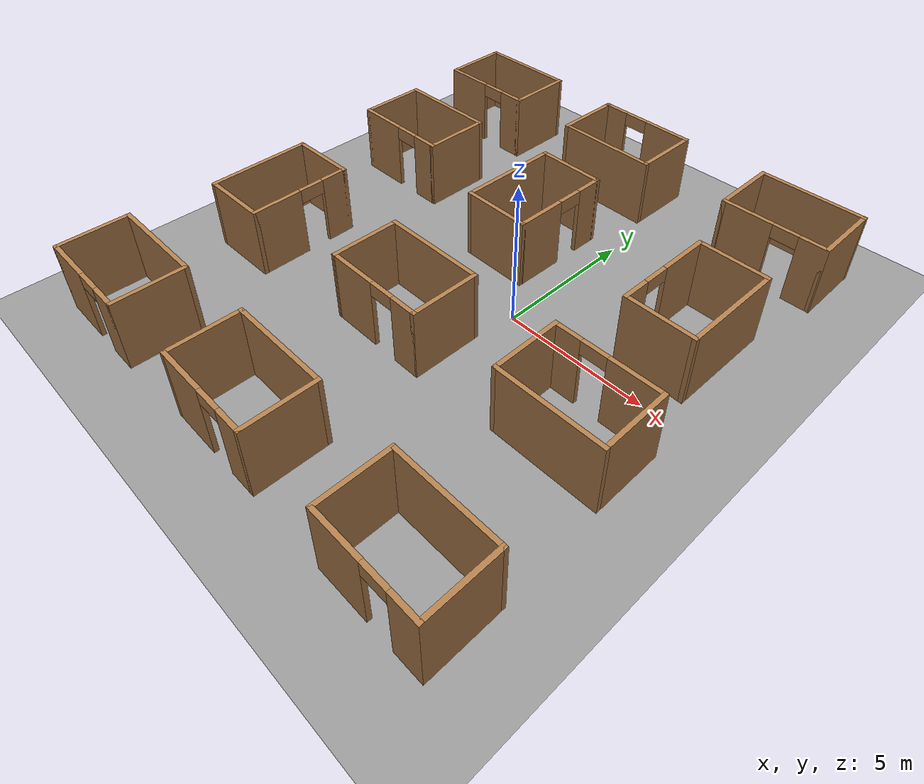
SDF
<sdf version="1.6">
 <world name="default">
  <light name="sun" type="directional">
   <pose>0 0 10 0 -0 0</pose>
   <diffuse>0.8 0.8 0.8 1</diffuse>
   <specular>0.2 0.2 0.2 1</specular>
   <attenuation>
    <range>1000</range>
    <constant>0.9</constant>
    <linear>0.01</linear>
    <quadratic>0.001</quadratic>
   </attenuation>
   <direction>0.5 0.1 -0.9</direction>
  </light>
  <scene><ambient>0.4 0.4 0.4 1</ambient><background>0.7 0.7 0.7 1</background><shadows>1</shadows></scene>
  <physics name="default_physics" default="0" type="ode">
   <max_step_size>0.01</max_step_size>
   <real_time_factor>1</real_time_factor>
   <real_time_update_rate>100</real_time_update_rate>
  </physics>
  <model name="ground_plane_0">
   <static>1</static>
   <link name="link">
    <collision name="collision">
     <geometry><plane><normal>0 0 1</normal><size>100 100</size></plane></geometry>
     <surface><friction><ode><mu>100</mu><mu2>50</mu2></ode></friction></surface>
    </collision>
    <visual name="visual">
     <cast_shadows>0</cast_shadows>
     <geometry><plane><normal>0 0 1</normal><size>100 100</size></plane></geometry>
     <material>
      <script><uri>file://media/materials/scripts/gazebo.material</uri><name>Gazebo/Grey</name></script>
     </material>
    </visual>
    <velocity_decay><linear>0</linear><angular>0</angular></velocity_decay>
   </link>
   <pose>0.497681 0 0 0 -0 0</pose>
  </model>
  <gravity>0 0 -9.8</gravity>
  <magnetic_field>6e-06 2.3e-05 -4.2e-05</magnetic_field>
  <atmosphere type="adiabatic"/>
  <spherical_coordinates>
   <surface_model>EARTH_WGS84</surface_model>
   <latitude_deg>0</latitude_deg>
   <longitude_deg>0</longitude_deg>
   <elevation>0</elevation>
   <heading_deg>0</heading_deg>
  </spherical_coordinates>
  <model name="Small_Room">
   <pose>-2.17108 3.1826 0 0 -0 1.55876</pose>
   <link name="Wall_0">
    <pose>0 -1.175 0 0 -0 0</pose>
    <visual name="Wall_0_Visual_0">
     <pose>-0.9525 0 1.25 0 -0 0</pose>
     <geometry><box><size>1.845 0.15 2.5</size></box></geometry>
     <material>
      <script><uri>file://media/materials/scripts/gazebo.material</uri><name>Gazebo/Wood</name></script>
      <ambient>1 1 1 1</ambient>
     </material>
     <meta><layer>0</layer></meta>
    </visual>
    <collision name="Wall_0_Collision_0">
     <geometry><box><size>1.845 0.15 2.5</size></box></geometry>
     <pose>-0.9525 0 1.25 0 -0 0</pose>
    </collision>
    <visual name="Wall_0_Visual_1">
     <pose>1.3725 0 1.25 0 -0 0</pose>
     <geometry><box><size>1.005 0.15 2.5</size></box></geometry>
     <material>
      <script><uri>file://media/materials/scripts/gazebo.material</uri><name>Gazebo/Wood</name></script>
      <ambient>1 1 1 1</ambient>
     </material>
     <meta><layer>0</layer></meta>
    </visual>
    <collision name="Wall_0_Collision_1">
     <geometry><box><size>1.005 0.15 2.5</size></box></geometry>
     <pose>1.3725 0 1.25 0 -0 0</pose>
    </collision>
    <visual name="Wall_0_Visual_2">
     <pose>0.42 0 2.25 0 -0 0</pose>
     <geometry><box><size>0.9 0.15 0.5</size></box></geometry>
     <material>
      <script><uri>file://media/materials/scripts/gazebo.material</uri><name>Gazebo/Wood</name></script>
      <ambient>1 1 1 1</ambient>
     </material>
     <meta><layer>0</layer></meta>
    </visual>
    <collision name="Wall_0_Collision_2">
     <geometry><box><size>0.9 0.15 0.5</size></box></geometry>
     <pose>0.42 0 2.25 0 -0 0</pose>
    </collision>
   </link>
   <link name="Wall_1">
    <collision name="Wall_1_Collision">
     <geometry><box><size>2.5 0.15 2.5</size></box></geometry>
     <pose>0 0 1.25 0 -0 0</pose>
    </collision>
    <visual name="Wall_1_Visual">
     <pose>0 0 1.25 0 -0 0</pose>
     <geometry><box><size>2.5 0.15 2.5</size></box></geometry>
     <material>
      <script><uri>file://media/materials/scripts/gazebo.material</uri><name>Gazebo/Wood</name></script>
      <ambient>1 1 1 1</ambient>
     </material>
     <meta><layer>0</layer></meta>
    </visual>
    <pose>1.8 0 0 0 -0 1.5708</pose>
   </link>
   <link name="Wall_2">
    <collision name="Wall_2_Collision">
     <geometry><box><size>3.75 0.15 2.5</size></box></geometry>
     <pose>0 0 1.25 0 -0 0</pose>
    </collision>
    <visual name="Wall_2_Visual">
     <pose>0 0 1.25 0 -0 0</pose>
     <geometry><box><size>3.75 0.15 2.5</size></box></geometry>
     <material>
      <script><uri>file://media/materials/scripts/gazebo.material</uri><name>Gazebo/Wood</name></script>
      <ambient>0.760784 0.662745 0.627451 1</ambient>
     </material>
     <meta><layer>0</layer></meta>
    </visual>
    <pose>0 1.175 0 0 -0 3.14159</pose>
   </link>
   <link name="Wall_3">
    <collision name="Wall_3_Collision">
     <geometry><box><size>2.5 0.15 2.5</size></box></geometry>
     <pose>0 0 1.25 0 -0 0</pose>
    </collision>
    <visual name="Wall_3_Visual">
     <pose>0 0 1.25 0 -0 0</pose>
     <geometry><box><size>2.5 0.15 2.5</size></box></geometry>
     <material>
      <script><uri>file://media/materials/scripts/gazebo.material</uri><name>Gazebo/Wood</name></script>
      <ambient>0.760784 0.662745 0.627451 1</ambient>
     </material>
     <meta><layer>0</layer></meta>
    </visual>
    <pose>-1.8 0 0 0 0 -1.5708</pose>
   </link>
   <static>1</static>
  </model>
  <model name="Small_Room_clone_0">
   <pose>4.49489 -2.40828 0 0 0 -3.13544</pose>
   <link name="Wall_0">
    <pose>0 -1.175 0 0 -0 0</pose>
    <visual name="Wall_0_Visual_0">
     <pose>-0.9525 0 1.25 0 -0 0</pose>
     <geometry><box><size>1.845 0.15 2.5</size></box></geometry>
     <material>
      <script><uri>file://media/materials/scripts/gazebo.material</uri><name>Gazebo/Wood</name></script>
      <ambient>1 1 1 1</ambient>
     </material>
     <meta><layer>0</layer></meta>
    </visual>
    <collision name="Wall_0_Collision_0">
     <geometry><box><size>1.845 0.15 2.5</size></box></geometry>
     <pose>-0.9525 0 1.25 0 -0 0</pose>
    </collision>
    <visual name="Wall_0_Visual_1">
     <pose>1.3725 0 1.25 0 -0 0</pose>
     <geometry><box><size>1.005 0.15 2.5</size></box></geometry>
     <material>
      <script><uri>file://media/materials/scripts/gazebo.material</uri><name>Gazebo/Wood</name></script>
      <ambient>1 1 1 1</ambient>
     </material>
     <meta><layer>0</layer></meta>
    </visual>
    <collision name="Wall_0_Collision_1">
     <geometry><box><size>1.005 0.15 2.5</size></box></geometry>
     <pose>1.3725 0 1.25 0 -0 0</pose>
    </collision>
    <visual name="Wall_0_Visual_2">
     <pose>0.42 0 2.25 0 -0 0</pose>
     <geometry><box><size>0.9 0.15 0.5</size></box></geometry>
     <material>
      <script><uri>file://media/materials/scripts/gazebo.material</uri><name>Gazebo/Wood</name></script>
      <ambient>1 1 1 1</ambient>
     </material>
     <meta><layer>0</layer></meta>
    </visual>
    <collision name="Wall_0_Collision_2">
     <geometry><box><size>0.9 0.15 0.5</size></box></geometry>
     <pose>0.42 0 2.25 0 -0 0</pose>
    </collision>
   </link>
   <link name="Wall_1">
    <collision name="Wall_1_Collision">
     <geometry><box><size>2.5 0.15 2.5</size></box></geometry>
     <pose>0 0 1.25 0 -0 0</pose>
    </collision>
    <visual name="Wall_1_Visual">
     <pose>0 0 1.25 0 -0 0</pose>
     <geometry><box><size>2.5 0.15 2.5</size></box></geometry>
     <material>
      <script><uri>file://media/materials/scripts/gazebo.material</uri><name>Gazebo/Wood</name></script>
      <ambient>1 1 1 1</ambient>
     </material>
     <meta><layer>0</layer></meta>
    </visual>
    <pose>1.8 0 0 0 -0 1.5708</pose>
   </link>
   <link name="Wall_2">
    <collision name="Wall_2_Collision">
     <geometry><box><size>3.75 0.15 2.5</size></box></geometry>
     <pose>0 0 1.25 0 -0 0</pose>
    </collision>
    <visual name="Wall_2_Visual">
     <pose>0 0 1.25 0 -0 0</pose>
     <geometry><box><size>3.75 0.15 2.5</size></box></geometry>
     <material>
      <script><uri>file://media/materials/scripts/gazebo.material</uri><name>Gazebo/Wood</name></script>
      <ambient>0.760784 0.662745 0.627451 1</ambient>
     </material>
     <meta><layer>0</layer></meta>
    </visual>
    <pose>0 1.175 0 0 -0 3.14159</pose>
   </link>
   <link name="Wall_3">
    <collision name="Wall_3_Collision">
     <geometry><box><size>2.5 0.15 2.5</size></box></geometry>
     <pose>0 0 1.25 0 -0 0</pose>
    </collision>
    <visual name="Wall_3_Visual">
     <pose>0 0 1.25 0 -0 0</pose>
     <geometry><box><size>2.5 0.15 2.5</size></box></geometry>
     <material>
      <script><uri>file://media/materials/scripts/gazebo.material</uri><name>Gazebo/Wood</name></script>
      <ambient>0.760784 0.662745 0.627451 1</ambient>
     </material>
     <meta><layer>0</layer></meta>
    </visual>
    <pose>-1.8 0 0 0 0 -1.5708</pose>
   </link>
   <static>1</static>
  </model>
  <model name="Small_Room_clone_1">
   <pose>4.53627 2.79284 0 0 0 -1.5813</pose>
   <link name="Wall_0">
    <pose>0 -1.175 0 0 -0 0</pose>
    <visual name="Wall_0_Visual_0">
     <pose>-0.9525 0 1.25 0 -0 0</pose>
     <geometry><box><size>1.845 0.15 2.5</size></box></geometry>
     <material>
      <script><uri>file://media/materials/scripts/gazebo.material</uri><name>Gazebo/Wood</name></script>
      <ambient>1 1 1 1</ambient>
     </material>
     <meta><layer>0</layer></meta>
    </visual>
    <collision name="Wall_0_Collision_0">
     <geometry><box><size>1.845 0.15 2.5</size></box></geometry>
     <pose>-0.9525 0 1.25 0 -0 0</pose>
    </collision>
    <visual name="Wall_0_Visual_1">
     <pose>1.3725 0 1.25 0 -0 0</pose>
     <geometry><box><size>1.005 0.15 2.5</size></box></geometry>
     <material>
      <script><uri>file://media/materials/scripts/gazebo.material</uri><name>Gazebo/Wood</name></script>
      <ambient>1 1 1 1</ambient>
     </material>
     <meta><layer>0</layer></meta>
    </visual>
    <collision name="Wall_0_Collision_1">
     <geometry><box><size>1.005 0.15 2.5</size></box></geometry>
     <pose>1.3725 0 1.25 0 -0 0</pose>
    </collision>
    <visual name="Wall_0_Visual_2">
     <pose>0.42 0 2.25 0 -0 0</pose>
     <geometry><box><size>0.9 0.15 0.5</size></box></geometry>
     <material>
      <script><uri>file://media/materials/scripts/gazebo.material</uri><name>Gazebo/Wood</name></script>
      <ambient>1 1 1 1</ambient>
     </material>
     <meta><layer>0</layer></meta>
    </visual>
    <collision name="Wall_0_Collision_2">
     <geometry><box><size>0.9 0.15 0.5</size></box></geometry>
     <pose>0.42 0 2.25 0 -0 0</pose>
    </collision>
   </link>
   <link name="Wall_1">
    <collision name="Wall_1_Collision">
     <geometry><box><size>2.5 0.15 2.5</size></box></geometry>
     <pose>0 0 1.25 0 -0 0</pose>
    </collision>
    <visual name="Wall_1_Visual">
     <pose>0 0 1.25 0 -0 0</pose>
     <geometry><box><size>2.5 0.15 2.5</size></box></geometry>
     <material>
      <script><uri>file://media/materials/scripts/gazebo.material</uri><name>Gazebo/Wood</name></script>
      <ambient>1 1 1 1</ambient>
     </material>
     <meta><layer>0</layer></meta>
    </visual>
    <pose>1.8 0 0 0 -0 1.5708</pose>
   </link>
   <link name="Wall_2">
    <collision name="Wall_2_Collision">
     <geometry><box><size>3.75 0.15 2.5</size></box></geometry>
     <pose>0 0 1.25 0 -0 0</pose>
    </collision>
    <visual name="Wall_2_Visual">
     <pose>0 0 1.25 0 -0 0</pose>
     <geometry><box><size>3.75 0.15 2.5</size></box></geometry>
     <material>
      <script><uri>file://media/materials/scripts/gazebo.material</uri><name>Gazebo/Wood</name></script>
      <ambient>0.760784 0.662745 0.627451 1</ambient>
     </material>
     <meta><layer>0</layer></meta>
    </visual>
    <pose>0 1.175 0 0 -0 3.14159</pose>
   </link>
   <link name="Wall_3">
    <collision name="Wall_3_Collision">
     <geometry><box><size>2.5 0.15 2.5</size></box></geometry>
     <pose>0 0 1.25 0 -0 0</pose>
    </collision>
    <visual name="Wall_3_Visual">
     <pose>0 0 1.25 0 -0 0</pose>
     <geometry><box><size>2.5 0.15 2.5</size></box></geometry>
     <material>
      <script><uri>file://media/materials/scripts/gazebo.material</uri><name>Gazebo/Wood</name></script>
      <ambient>0.760784 0.662745 0.627451 1</ambient>
     </material>
     <meta><layer>0</layer></meta>
    </visual>
    <pose>-1.8 0 0 0 0 -1.5708</pose>
   </link>
   <static>1</static>
  </model>
  <model name="Small_Room_clone_2">
   <pose>4.48448 8.2328 0 0 -0 0</pose>
   <link name="Wall_0">
    <pose>0 -1.175 0 0 -0 0</pose>
    <visual name="Wall_0_Visual_0">
     <pose>-0.9525 0 1.25 0 -0 0</pose>
     <geometry><box><size>1.845 0.15 2.5</size></box></geometry>
     <material>
      <script><uri>file://media/materials/scripts/gazebo.material</uri><name>Gazebo/Wood</name></script>
      <ambient>1 1 1 1</ambient>
     </material>
     <meta><layer>0</layer></meta>
    </visual>
    <collision name="Wall_0_Collision_0">
     <geometry><box><size>1.845 0.15 2.5</size></box></geometry>
     <pose>-0.9525 0 1.25 0 -0 0</pose>
    </collision>
    <visual name="Wall_0_Visual_1">
     <pose>1.3725 0 1.25 0 -0 0</pose>
     <geometry><box><size>1.005 0.15 2.5</size></box></geometry>
     <material>
      <script><uri>file://media/materials/scripts/gazebo.material</uri><name>Gazebo/Wood</name></script>
      <ambient>1 1 1 1</ambient>
     </material>
     <meta><layer>0</layer></meta>
    </visual>
    <collision name="Wall_0_Collision_1">
     <geometry><box><size>1.005 0.15 2.5</size></box></geometry>
     <pose>1.3725 0 1.25 0 -0 0</pose>
    </collision>
    <visual name="Wall_0_Visual_2">
     <pose>0.42 0 2.25 0 -0 0</pose>
     <geometry><box><size>0.9 0.15 0.5</size></box></geometry>
     <material>
      <script><uri>file://media/materials/scripts/gazebo.material</uri><name>Gazebo/Wood</name></script>
      <ambient>1 1 1 1</ambient>
     </material>
     <meta><layer>0</layer></meta>
    </visual>
    <collision name="Wall_0_Collision_2">
     <geometry><box><size>0.9 0.15 0.5</size></box></geometry>
     <pose>0.42 0 2.25 0 -0 0</pose>
    </collision>
   </link>
   <link name="Wall_1">
    <collision name="Wall_1_Collision">
     <geometry><box><size>2.5 0.15 2.5</size></box></geometry>
     <pose>0 0 1.25 0 -0 0</pose>
    </collision>
    <visual name="Wall_1_Visual">
     <pose>0 0 1.25 0 -0 0</pose>
     <geometry><box><size>2.5 0.15 2.5</size></box></geometry>
     <material>
      <script><uri>file://media/materials/scripts/gazebo.material</uri><name>Gazebo/Wood</name></script>
      <ambient>1 1 1 1</ambient>
     </material>
     <meta><layer>0</layer></meta>
    </visual>
    <pose>1.8 0 0 0 -0 1.5708</pose>
   </link>
   <link name="Wall_2">
    <collision name="Wall_2_Collision">
     <geometry><box><size>3.75 0.15 2.5</size></box></geometry>
     <pose>0 0 1.25 0 -0 0</pose>
    </collision>
    <visual name="Wall_2_Visual">
     <pose>0 0 1.25 0 -0 0</pose>
     <geometry><box><size>3.75 0.15 2.5</size></box></geometry>
     <material>
      <script><uri>file://media/materials/scripts/gazebo.material</uri><name>Gazebo/Wood</name></script>
      <ambient>0.760784 0.662745 0.627451 1</ambient>
     </material>
     <meta><layer>0</layer></meta>
    </visual>
    <pose>0 1.175 0 0 -0 3.14159</pose>
   </link>
   <link name="Wall_3">
    <collision name="Wall_3_Collision">
     <geometry><box><size>2.5 0.15 2.5</size></box></geometry>
     <pose>0 0 1.25 0 -0 0</pose>
    </collision>
    <visual name="Wall_3_Visual">
     <pose>0 0 1.25 0 -0 0</pose>
     <geometry><box><size>2.5 0.15 2.5</size></box></geometry>
     <material>
      <script><uri>file://media/materials/scripts/gazebo.material</uri><name>Gazebo/Wood</name></script>
      <ambient>0.760784 0.662745 0.627451 1</ambient>
     </material>
     <meta><layer>0</layer></meta>
    </visual>
    <pose>-1.8 0 0 0 0 -1.5708</pose>
   </link>
   <static>1</static>
  </model>
  <model name="Small_Room_clone_3">
   <pose>-2.21611 8.1824 0 0 -0 3.12949</pose>
   <link name="Wall_0">
    <pose>0 -1.175 0 0 -0 0</pose>
    <visual name="Wall_0_Visual_0">
     <pose>-0.9525 0 1.25 0 -0 0</pose>
     <geometry><box><size>1.845 0.15 2.5</size></box></geometry>
     <material>
      <script><uri>file://media/materials/scripts/gazebo.material</uri><name>Gazebo/Wood</name></script>
      <ambient>1 1 1 1</ambient>
     </material>
     <meta><layer>0</layer></meta>
    </visual>
    <collision name="Wall_0_Collision_0">
     <geometry><box><size>1.845 0.15 2.5</size></box></geometry>
     <pose>-0.9525 0 1.25 0 -0 0</pose>
    </collision>
    <visual name="Wall_0_Visual_1">
     <pose>1.3725 0 1.25 0 -0 0</pose>
     <geometry><box><size>1.005 0.15 2.5</size></box></geometry>
     <material>
      <script><uri>file://media/materials/scripts/gazebo.material</uri><name>Gazebo/Wood</name></script>
      <ambient>1 1 1 1</ambient>
     </material>
     <meta><layer>0</layer></meta>
    </visual>
    <collision name="Wall_0_Collision_1">
     <geometry><box><size>1.005 0.15 2.5</size></box></geometry>
     <pose>1.3725 0 1.25 0 -0 0</pose>
    </collision>
    <visual name="Wall_0_Visual_2">
     <pose>0.42 0 2.25 0 -0 0</pose>
     <geometry><box><size>0.9 0.15 0.5</size></box></geometry>
     <material>
      <script><uri>file://media/materials/scripts/gazebo.material</uri><name>Gazebo/Wood</name></script>
      <ambient>1 1 1 1</ambient>
     </material>
     <meta><layer>0</layer></meta>
    </visual>
    <collision name="Wall_0_Collision_2">
     <geometry><box><size>0.9 0.15 0.5</size></box></geometry>
     <pose>0.42 0 2.25 0 -0 0</pose>
    </collision>
   </link>
   <link name="Wall_1">
    <collision name="Wall_1_Collision">
     <geometry><box><size>2.5 0.15 2.5</size></box></geometry>
     <pose>0 0 1.25 0 -0 0</pose>
    </collision>
    <visual name="Wall_1_Visual">
     <pose>0 0 1.25 0 -0 0</pose>
     <geometry><box><size>2.5 0.15 2.5</size></box></geometry>
     <material>
      <script><uri>file://media/materials/scripts/gazebo.material</uri><name>Gazebo/Wood</name></script>
      <ambient>1 1 1 1</ambient>
     </material>
     <meta><layer>0</layer></meta>
    </visual>
    <pose>1.8 0 0 0 -0 1.5708</pose>
   </link>
   <link name="Wall_2">
    <collision name="Wall_2_Collision">
     <geometry><box><size>3.75 0.15 2.5</size></box></geometry>
     <pose>0 0 1.25 0 -0 0</pose>
    </collision>
    <visual name="Wall_2_Visual">
     <pose>0 0 1.25 0 -0 0</pose>
     <geometry><box><size>3.75 0.15 2.5</size></box></geometry>
     <material>
      <script><uri>file://media/materials/scripts/gazebo.material</uri><name>Gazebo/Wood</name></script>
      <ambient>0.760784 0.662745 0.627451 1</ambient>
     </material>
     <meta><layer>0</layer></meta>
    </visual>
    <pose>0 1.175 0 0 -0 3.14159</pose>
   </link>
   <link name="Wall_3">
    <collision name="Wall_3_Collision">
     <geometry><box><size>2.5 0.15 2.5</size></box></geometry>
     <pose>0 0 1.25 0 -0 0</pose>
    </collision>
    <visual name="Wall_3_Visual">
     <pose>0 0 1.25 0 -0 0</pose>
     <geometry><box><size>2.5 0.15 2.5</size></box></geometry>
     <material>
      <script><uri>file://media/materials/scripts/gazebo.material</uri><name>Gazebo/Wood</name></script>
      <ambient>0.760784 0.662745 0.627451 1</ambient>
     </material>
     <meta><layer>0</layer></meta>
    </visual>
    <pose>-1.8 0 0 0 0 -1.5708</pose>
   </link>
   <static>1</static>
  </model>
  <model name="Small_Room_clone_4">
   <pose>-8.41545 8.31884 0 0 -0 0</pose>
   <link name="Wall_0">
    <pose>0 -1.175 0 0 -0 0</pose>
    <visual name="Wall_0_Visual_0">
     <pose>-0.9525 0 1.25 0 -0 0</pose>
     <geometry><box><size>1.845 0.15 2.5</size></box></geometry>
     <material>
      <script><uri>file://media/materials/scripts/gazebo.material</uri><name>Gazebo/Wood</name></script>
      <ambient>1 1 1 1</ambient>
     </material>
     <meta><layer>0</layer></meta>
    </visual>
    <collision name="Wall_0_Collision_0">
     <geometry><box><size>1.845 0.15 2.5</size></box></geometry>
     <pose>-0.9525 0 1.25 0 -0 0</pose>
    </collision>
    <visual name="Wall_0_Visual_1">
     <pose>1.3725 0 1.25 0 -0 0</pose>
     <geometry><box><size>1.005 0.15 2.5</size></box></geometry>
     <material>
      <script><uri>file://media/materials/scripts/gazebo.material</uri><name>Gazebo/Wood</name></script>
      <ambient>1 1 1 1</ambient>
     </material>
     <meta><layer>0</layer></meta>
    </visual>
    <collision name="Wall_0_Collision_1">
     <geometry><box><size>1.005 0.15 2.5</size></box></geometry>
     <pose>1.3725 0 1.25 0 -0 0</pose>
    </collision>
    <visual name="Wall_0_Visual_2">
     <pose>0.42 0 2.25 0 -0 0</pose>
     <geometry><box><size>0.9 0.15 0.5</size></box></geometry>
     <material>
      <script><uri>file://media/materials/scripts/gazebo.material</uri><name>Gazebo/Wood</name></script>
      <ambient>1 1 1 1</ambient>
     </material>
     <meta><layer>0</layer></meta>
    </visual>
    <collision name="Wall_0_Collision_2">
     <geometry><box><size>0.9 0.15 0.5</size></box></geometry>
     <pose>0.42 0 2.25 0 -0 0</pose>
    </collision>
   </link>
   <link name="Wall_1">
    <collision name="Wall_1_Collision">
     <geometry><box><size>2.5 0.15 2.5</size></box></geometry>
     <pose>0 0 1.25 0 -0 0</pose>
    </collision>
    <visual name="Wall_1_Visual">
     <pose>0 0 1.25 0 -0 0</pose>
     <geometry><box><size>2.5 0.15 2.5</size></box></geometry>
     <material>
      <script><uri>file://media/materials/scripts/gazebo.material</uri><name>Gazebo/Wood</name></script>
      <ambient>1 1 1 1</ambient>
     </material>
     <meta><layer>0</layer></meta>
    </visual>
    <pose>1.8 0 0 0 -0 1.5708</pose>
   </link>
   <link name="Wall_2">
    <collision name="Wall_2_Collision">
     <geometry><box><size>3.75 0.15 2.5</size></box></geometry>
     <pose>0 0 1.25 0 -0 0</pose>
    </collision>
    <visual name="Wall_2_Visual">
     <pose>0 0 1.25 0 -0 0</pose>
     <geometry><box><size>3.75 0.15 2.5</size></box></geometry>
     <material>
      <script><uri>file://media/materials/scripts/gazebo.material</uri><name>Gazebo/Wood</name></script>
      <ambient>0.760784 0.662745 0.627451 1</ambient>
     </material>
     <meta><layer>0</layer></meta>
    </visual>
    <pose>0 1.175 0 0 -0 3.14159</pose>
   </link>
   <link name="Wall_3">
    <collision name="Wall_3_Collision">
     <geometry><box><size>2.5 0.15 2.5</size></box></geometry>
     <pose>0 0 1.25 0 -0 0</pose>
    </collision>
    <visual name="Wall_3_Visual">
     <pose>0 0 1.25 0 -0 0</pose>
     <geometry><box><size>2.5 0.15 2.5</size></box></geometry>
     <material>
      <script><uri>file://media/materials/scripts/gazebo.material</uri><name>Gazebo/Wood</name></script>
      <ambient>0.760784 0.662745 0.627451 1</ambient>
     </material>
     <meta><layer>0</layer></meta>
    </visual>
    <pose>-1.8 0 0 0 0 -1.5708</pose>
   </link>
   <static>1</static>
  </model>
  <model name="Small_Room_clone_5">
   <pose>-8.25219 3.63806 0 0 -0 0</pose>
   <link name="Wall_0">
    <pose>0 -1.175 0 0 -0 0</pose>
    <visual name="Wall_0_Visual_0">
     <pose>-0.9525 0 1.25 0 -0 0</pose>
     <geometry><box><size>1.845 0.15 2.5</size></box></geometry>
     <material>
      <script><uri>file://media/materials/scripts/gazebo.material</uri><name>Gazebo/Wood</name></script>
      <ambient>1 1 1 1</ambient>
     </material>
     <meta><layer>0</layer></meta>
    </visual>
    <collision name="Wall_0_Collision_0">
     <geometry><box><size>1.845 0.15 2.5</size></box></geometry>
     <pose>-0.9525 0 1.25 0 -0 0</pose>
    </collision>
    <visual name="Wall_0_Visual_1">
     <pose>1.3725 0 1.25 0 -0 0</pose>
     <geometry><box><size>1.005 0.15 2.5</size></box></geometry>
     <material>
      <script><uri>file://media/materials/scripts/gazebo.material</uri><name>Gazebo/Wood</name></script>
      <ambient>1 1 1 1</ambient>
     </material>
     <meta><layer>0</layer></meta>
    </visual>
    <collision name="Wall_0_Collision_1">
     <geometry><box><size>1.005 0.15 2.5</size></box></geometry>
     <pose>1.3725 0 1.25 0 -0 0</pose>
    </collision>
    <visual name="Wall_0_Visual_2">
     <pose>0.42 0 2.25 0 -0 0</pose>
     <geometry><box><size>0.9 0.15 0.5</size></box></geometry>
     <material>
      <script><uri>file://media/materials/scripts/gazebo.material</uri><name>Gazebo/Wood</name></script>
      <ambient>1 1 1 1</ambient>
     </material>
     <meta><layer>0</layer></meta>
    </visual>
    <collision name="Wall_0_Collision_2">
     <geometry><box><size>0.9 0.15 0.5</size></box></geometry>
     <pose>0.42 0 2.25 0 -0 0</pose>
    </collision>
   </link>
   <link name="Wall_1">
    <collision name="Wall_1_Collision">
     <geometry><box><size>2.5 0.15 2.5</size></box></geometry>
     <pose>0 0 1.25 0 -0 0</pose>
    </collision>
    <visual name="Wall_1_Visual">
     <pose>0 0 1.25 0 -0 0</pose>
     <geometry><box><size>2.5 0.15 2.5</size></box></geometry>
     <material>
      <script><uri>file://media/materials/scripts/gazebo.material</uri><name>Gazebo/Wood</name></script>
      <ambient>1 1 1 1</ambient>
     </material>
     <meta><layer>0</layer></meta>
    </visual>
    <pose>1.8 0 0 0 -0 1.5708</pose>
   </link>
   <link name="Wall_2">
    <collision name="Wall_2_Collision">
     <geometry><box><size>3.75 0.15 2.5</size></box></geometry>
     <pose>0 0 1.25 0 -0 0</pose>
    </collision>
    <visual name="Wall_2_Visual">
     <pose>0 0 1.25 0 -0 0</pose>
     <geometry><box><size>3.75 0.15 2.5</size></box></geometry>
     <material>
      <script><uri>file://media/materials/scripts/gazebo.material</uri><name>Gazebo/Wood</name></script>
      <ambient>0.760784 0.662745 0.627451 1</ambient>
     </material>
     <meta><layer>0</layer></meta>
    </visual>
    <pose>0 1.175 0 0 -0 3.14159</pose>
   </link>
   <link name="Wall_3">
    <collision name="Wall_3_Collision">
     <geometry><box><size>2.5 0.15 2.5</size></box></geometry>
     <pose>0 0 1.25 0 -0 0</pose>
    </collision>
    <visual name="Wall_3_Visual">
     <pose>0 0 1.25 0 -0 0</pose>
     <geometry><box><size>2.5 0.15 2.5</size></box></geometry>
     <material>
      <script><uri>file://media/materials/scripts/gazebo.material</uri><name>Gazebo/Wood</name></script>
      <ambient>0.760784 0.662745 0.627451 1</ambient>
     </material>
     <meta><layer>0</layer></meta>
    </visual>
    <pose>-1.8 0 0 0 0 -1.5708</pose>
   </link>
   <static>1</static>
  </model>
  <model name="Small_Room_clone_6">
   <pose>-2.07532 -2.61831 0 0 -0 0</pose>
   <link name="Wall_0">
    <pose>0 -1.175 0 0 -0 0</pose>
    <visual name="Wall_0_Visual_0">
     <pose>-0.9525 0 1.25 0 -0 0</pose>
     <geometry><box><size>1.845 0.15 2.5</size></box></geometry>
     <material>
      <script><uri>file://media/materials/scripts/gazebo.material</uri><name>Gazebo/Wood</name></script>
      <ambient>1 1 1 1</ambient>
     </material>
     <meta><layer>0</layer></meta>
    </visual>
    <collision name="Wall_0_Collision_0">
     <geometry><box><size>1.845 0.15 2.5</size></box></geometry>
     <pose>-0.9525 0 1.25 0 -0 0</pose>
    </collision>
    <visual name="Wall_0_Visual_1">
     <pose>1.3725 0 1.25 0 -0 0</pose>
     <geometry><box><size>1.005 0.15 2.5</size></box></geometry>
     <material>
      <script><uri>file://media/materials/scripts/gazebo.material</uri><name>Gazebo/Wood</name></script>
      <ambient>1 1 1 1</ambient>
     </material>
     <meta><layer>0</layer></meta>
    </visual>
    <collision name="Wall_0_Collision_1">
     <geometry><box><size>1.005 0.15 2.5</size></box></geometry>
     <pose>1.3725 0 1.25 0 -0 0</pose>
    </collision>
    <visual name="Wall_0_Visual_2">
     <pose>0.42 0 2.25 0 -0 0</pose>
     <geometry><box><size>0.9 0.15 0.5</size></box></geometry>
     <material>
      <script><uri>file://media/materials/scripts/gazebo.material</uri><name>Gazebo/Wood</name></script>
      <ambient>1 1 1 1</ambient>
     </material>
     <meta><layer>0</layer></meta>
    </visual>
    <collision name="Wall_0_Collision_2">
     <geometry><box><size>0.9 0.15 0.5</size></box></geometry>
     <pose>0.42 0 2.25 0 -0 0</pose>
    </collision>
   </link>
   <link name="Wall_1">
    <collision name="Wall_1_Collision">
     <geometry><box><size>2.5 0.15 2.5</size></box></geometry>
     <pose>0 0 1.25 0 -0 0</pose>
    </collision>
    <visual name="Wall_1_Visual">
     <pose>0 0 1.25 0 -0 0</pose>
     <geometry><box><size>2.5 0.15 2.5</size></box></geometry>
     <material>
      <script><uri>file://media/materials/scripts/gazebo.material</uri><name>Gazebo/Wood</name></script>
      <ambient>1 1 1 1</ambient>
     </material>
     <meta><layer>0</layer></meta>
    </visual>
    <pose>1.8 0 0 0 -0 1.5708</pose>
   </link>
   <link name="Wall_2">
    <collision name="Wall_2_Collision">
     <geometry><box><size>3.75 0.15 2.5</size></box></geometry>
     <pose>0 0 1.25 0 -0 0</pose>
    </collision>
    <visual name="Wall_2_Visual">
     <pose>0 0 1.25 0 -0 0</pose>
     <geometry><box><size>3.75 0.15 2.5</size></box></geometry>
     <material>
      <script><uri>file://media/materials/scripts/gazebo.material</uri><name>Gazebo/Wood</name></script>
      <ambient>0.760784 0.662745 0.627451 1</ambient>
     </material>
     <meta><layer>0</layer></meta>
    </visual>
    <pose>0 1.175 0 0 -0 3.14159</pose>
   </link>
   <link name="Wall_3">
    <collision name="Wall_3_Collision">
     <geometry><box><size>2.5 0.15 2.5</size></box></geometry>
     <pose>0 0 1.25 0 -0 0</pose>
    </collision>
    <visual name="Wall_3_Visual">
     <pose>0 0 1.25 0 -0 0</pose>
     <geometry><box><size>2.5 0.15 2.5</size></box></geometry>
     <material>
      <script><uri>file://media/materials/scripts/gazebo.material</uri><name>Gazebo/Wood</name></script>
      <ambient>0.760784 0.662745 0.627451 1</ambient>
     </material>
     <meta><layer>0</layer></meta>
    </visual>
    <pose>-1.8 0 0 0 0 -1.5708</pose>
   </link>
   <static>1</static>
  </model>
  <model name="Small_Room_clone_6_clone_1_0">
   <link name="Wall_0">
    <pose>0 -1.175 0 0 -0 0</pose>
    <visual name="Wall_0_Visual_1">
     <pose>1.3725 0 1.25 0 -0 0</pose>
     <geometry><box><size>1.005 0.15 2.5</size></box></geometry>
     <material>
      <script><uri>file://media/materials/scripts/gazebo.material</uri><name>Gazebo/Wood</name></script>
      <ambient>1 1 1 1</ambient>
      <diffuse>1 1 1 1</diffuse>
      <specular>0.2 0.2 0.2 1</specular>
      <emissive>0 0 0 1</emissive>
     </material>
     <meta><layer>0</layer></meta>
    </visual>
    <visual name="Wall_0_Visual_0">
     <pose>-0.9525 0 1.25 0 -0 0</pose>
     <geometry><box><size>1.845 0.15 2.5</size></box></geometry>
     <material>
      <script><uri>file://media/materials/scripts/gazebo.material</uri><name>Gazebo/Wood</name></script>
      <ambient>1 1 1 1</ambient>
      <diffuse>1 1 1 1</diffuse>
      <specular>0.2 0.2 0.2 1</specular>
      <emissive>0 0 0 1</emissive>
     </material>
     <meta><layer>0</layer></meta>
    </visual>
    <visual name="Wall_0_Visual_2">
     <pose>0.42 0 2.25 0 -0 0</pose>
     <geometry><box><size>0.9 0.15 0.5</size></box></geometry>
     <material>
      <script><uri>file://media/materials/scripts/gazebo.material</uri><name>Gazebo/Wood</name></script>
      <ambient>1 1 1 1</ambient>
      <diffuse>1 1 1 1</diffuse>
      <specular>0.2 0.2 0.2 1</specular>
      <emissive>0 0 0 1</emissive>
     </material>
     <meta><layer>0</layer></meta>
    </visual>
    <collision name="Wall_0_Collision_0">
     <pose>-0.9525 0 1.25 0 -0 0</pose>
     <geometry><box><size>1.845 0.15 2.5</size></box></geometry>
     <surface>
      <friction>
       <ode><mu>1</mu><mu2>1</mu2><fdir1>0 0 0</fdir1><slip1>0</slip1><slip2>0</slip2></ode>
       <torsional>
        <coefficient>1</coefficient>
        <patch_radius>0</patch_radius>
        <surface_radius>0</surface_radius>
        <use_patch_radius>1</use_patch_radius>
        <ode><slip>0</slip></ode>
       </torsional>
      </friction>
      <bounce><restitution_coefficient>0</restitution_coefficient><threshold>1e+06</threshold></bounce>
      <contact>
       <collide_without_contact>0</collide_without_contact>
       <collide_without_contact_bitmask>1</collide_without_contact_bitmask>
       <collide_bitmask>1</collide_bitmask>
       <ode>
        <soft_cfm>0</soft_cfm>
        <soft_erp>0.2</soft_erp>
        <kp>1e+13</kp>
        <kd>1</kd>
        <max_vel>0.01</max_vel>
        <min_depth>0</min_depth>
       </ode>
       <bullet>
        <split_impulse>1</split_impulse>
        <split_impulse_penetration_threshold>-0.01</split_impulse_penetration_threshold>
        <soft_cfm>0</soft_cfm>
        <soft_erp>0.2</soft_erp>
        <kp>1e+13</kp>
        <kd>1</kd>
       </bullet>
      </contact>
     </surface>
    </collision>
    <collision name="Wall_0_Collision_1">
     <pose>1.3725 0 1.25 0 -0 0</pose>
     <geometry><box><size>1.005 0.15 2.5</size></box></geometry>
     <surface>
      <friction>
       <ode><mu>1</mu><mu2>1</mu2><fdir1>0 0 0</fdir1><slip1>0</slip1><slip2>0</slip2></ode>
       <torsional>
        <coefficient>1</coefficient>
        <patch_radius>0</patch_radius>
        <surface_radius>0</surface_radius>
        <use_patch_radius>1</use_patch_radius>
        <ode><slip>0</slip></ode>
       </torsional>
      </friction>
      <bounce><restitution_coefficient>0</restitution_coefficient><threshold>1e+06</threshold></bounce>
      <contact>
       <collide_without_contact>0</collide_without_contact>
       <collide_without_contact_bitmask>1</collide_without_contact_bitmask>
       <collide_bitmask>1</collide_bitmask>
       <ode>
        <soft_cfm>0</soft_cfm>
        <soft_erp>0.2</soft_erp>
        <kp>1e+13</kp>
        <kd>1</kd>
        <max_vel>0.01</max_vel>
        <min_depth>0</min_depth>
       </ode>
       <bullet>
        <split_impulse>1</split_impulse>
        <split_impulse_penetration_threshold>-0.01</split_impulse_penetration_threshold>
        <soft_cfm>0</soft_cfm>
        <soft_erp>0.2</soft_erp>
        <kp>1e+13</kp>
        <kd>1</kd>
       </bullet>
      </contact>
     </surface>
    </collision>
    <collision name="Wall_0_Collision_2">
     <pose>0.42 0 2.25 0 -0 0</pose>
     <geometry><box><size>0.9 0.15 0.5</size></box></geometry>
     <surface>
      <friction>
       <ode><mu>1</mu><mu2>1</mu2><fdir1>0 0 0</fdir1><slip1>0</slip1><slip2>0</slip2></ode>
       <torsional>
        <coefficient>1</coefficient>
        <patch_radius>0</patch_radius>
        <surface_radius>0</surface_radius>
        <use_patch_radius>1</use_patch_radius>
        <ode><slip>0</slip></ode>
       </torsional>
      </friction>
      <bounce><restitution_coefficient>0</restitution_coefficient><threshold>1e+06</threshold></bounce>
      <contact>
       <collide_without_contact>0</collide_without_contact>
       <collide_without_contact_bitmask>1</collide_without_contact_bitmask>
       <collide_bitmask>1</collide_bitmask>
       <ode>
        <soft_cfm>0</soft_cfm>
        <soft_erp>0.2</soft_erp>
        <kp>1e+13</kp>
        <kd>1</kd>
        <max_vel>0.01</max_vel>
        <min_depth>0</min_depth>
       </ode>
       <bullet>
        <split_impulse>1</split_impulse>
        <split_impulse_penetration_threshold>-0.01</split_impulse_penetration_threshold>
        <soft_cfm>0</soft_cfm>
        <soft_erp>0.2</soft_erp>
        <kp>1e+13</kp>
        <kd>1</kd>
       </bullet>
      </contact>
     </surface>
    </collision>
   </link>
   <link name="Wall_1">
    <pose>1.8 0 0 0 -0 1.5708</pose>
    <visual name="Wall_1_Visual">
     <pose>0 0 1.25 0 -0 0</pose>
     <geometry><box><size>2.5 0.15 2.5</size></box></geometry>
     <material>
      <script><uri>file://media/materials/scripts/gazebo.material</uri><name>Gazebo/Wood</name></script>
      <ambient>1 1 1 1</ambient>
      <diffuse>1 1 1 1</diffuse>
      <specular>0.2 0.2 0.2 1</specular>
      <emissive>0 0 0 1</emissive>
     </material>
     <meta><layer>0</layer></meta>
    </visual>
    <collision name="Wall_1_Collision">
     <pose>0 0 1.25 0 -0 0</pose>
     <geometry><box><size>2.5 0.15 2.5</size></box></geometry>
     <surface>
      <friction>
       <ode><mu>1</mu><mu2>1</mu2><fdir1>0 0 0</fdir1><slip1>0</slip1><slip2>0</slip2></ode>
       <torsional>
        <coefficient>1</coefficient>
        <patch_radius>0</patch_radius>
        <surface_radius>0</surface_radius>
        <use_patch_radius>1</use_patch_radius>
        <ode><slip>0</slip></ode>
       </torsional>
      </friction>
      <bounce><restitution_coefficient>0</restitution_coefficient><threshold>1e+06</threshold></bounce>
      <contact>
       <collide_without_contact>0</collide_without_contact>
       <collide_without_contact_bitmask>1</collide_without_contact_bitmask>
       <collide_bitmask>1</collide_bitmask>
       <ode>
        <soft_cfm>0</soft_cfm>
        <soft_erp>0.2</soft_erp>
        <kp>1e+13</kp>
        <kd>1</kd>
        <max_vel>0.01</max_vel>
        <min_depth>0</min_depth>
       </ode>
       <bullet>
        <split_impulse>1</split_impulse>
        <split_impulse_penetration_threshold>-0.01</split_impulse_penetration_threshold>
        <soft_cfm>0</soft_cfm>
        <soft_erp>0.2</soft_erp>
        <kp>1e+13</kp>
        <kd>1</kd>
       </bullet>
      </contact>
     </surface>
    </collision>
   </link>
   <link name="Wall_2">
    <pose>0 1.175 0 0 -0 3.14159</pose>
    <inertial>
     <mass>1</mass>
     <inertia><ixx>1</ixx><ixy>0</ixy><ixz>0</ixz><iyy>1</iyy><iyz>0</iyz><izz>1</izz></inertia>
    </inertial>
    <visual name="Wall_2_Visual">
     <pose>0 0 1.25 0 -0 0</pose>
     <geometry><box><size>3.75 0.15 2.5</size></box></geometry>
     <material>
      <script><uri>file://media/materials/scripts/gazebo.material</uri><name>Gazebo/Wood</name></script>
      <ambient>0.361 1 0.227 1</ambient>
      <diffuse>0.6 0.5 0.9 1</diffuse>
      <specular>0.6 0.4 0.2 1</specular>
      <emissive>0 0 0 1</emissive>
      <shader type="vertex"><normal_map>__default__</normal_map></shader>
     </material>
     <meta><layer>0</layer></meta>
    </visual>
    <collision name="Wall_2_Collision">
     <pose>0 0 1.25 0 -0 0</pose>
     <geometry><box><size>3.75 0.15 2.5</size></box></geometry>
     <surface>
      <friction>
       <ode><mu>1</mu><mu2>1</mu2><fdir1>0 0 0</fdir1><slip1>0</slip1><slip2>0</slip2></ode>
       <torsional>
        <coefficient>1</coefficient>
        <patch_radius>0</patch_radius>
        <surface_radius>0</surface_radius>
        <use_patch_radius>1</use_patch_radius>
        <ode><slip>0</slip></ode>
       </torsional>
      </friction>
      <bounce><restitution_coefficient>0</restitution_coefficient><threshold>1e+06</threshold></bounce>
      <contact>
       <collide_without_contact>0</collide_without_contact>
       <collide_without_contact_bitmask>1</collide_without_contact_bitmask>
       <collide_bitmask>1</collide_bitmask>
       <ode>
        <soft_cfm>0</soft_cfm>
        <soft_erp>0.2</soft_erp>
        <kp>1e+13</kp>
        <kd>1</kd>
        <max_vel>0.01</max_vel>
        <min_depth>0</min_depth>
       </ode>
       <bullet>
        <split_impulse>1</split_impulse>
        <split_impulse_penetration_threshold>-0.01</split_impulse_penetration_threshold>
        <soft_cfm>0</soft_cfm>
        <soft_erp>0.2</soft_erp>
        <kp>1e+13</kp>
        <kd>1</kd>
       </bullet>
      </contact>
     </surface>
    </collision>
   </link>
   <link name="Wall_3">
    <pose>-1.8 0 0 0 0 -1.5708</pose>
    <inertial>
     <mass>1</mass>
     <inertia><ixx>1</ixx><ixy>0</ixy><ixz>0</ixz><iyy>1</iyy><iyz>0</iyz><izz>1</izz></inertia>
    </inertial>
    <visual name="Wall_3_Visual">
     <pose>0 0 1.25 0 -0 0</pose>
     <geometry><box><size>2.5 0.15 2.5</size></box></geometry>
     <material>
      <script><uri>file://media/materials/scripts/gazebo.material</uri><name>Gazebo/Wood</name></script>
      <ambient>1 0.263 0.127 1</ambient>
      <diffuse>1 1 1 1</diffuse>
      <specular>0.2 0.2 0.2 1</specular>
      <emissive>0 0 0 1</emissive>
      <shader type="vertex"><normal_map>__default__</normal_map></shader>
     </material>
     <meta><layer>0</layer></meta>
    </visual>
    <collision name="Wall_3_Collision">
     <pose>0 0 1.25 0 -0 0</pose>
     <geometry><box><size>2.5 0.15 2.5</size></box></geometry>
     <surface>
      <friction>
       <ode><mu>1</mu><mu2>1</mu2><fdir1>0 0 0</fdir1><slip1>0</slip1><slip2>0</slip2></ode>
       <torsional>
        <coefficient>1</coefficient>
        <patch_radius>0</patch_radius>
        <surface_radius>0</surface_radius>
        <use_patch_radius>1</use_patch_radius>
        <ode><slip>0</slip></ode>
       </torsional>
      </friction>
      <bounce><restitution_coefficient>0</restitution_coefficient><threshold>1e+06</threshold></bounce>
      <contact>
       <collide_without_contact>0</collide_without_contact>
       <collide_without_contact_bitmask>1</collide_without_contact_bitmask>
       <collide_bitmask>1</collide_bitmask>
       <ode>
        <soft_cfm>0</soft_cfm>
        <soft_erp>0.2</soft_erp>
        <kp>1e+13</kp>
        <kd>1</kd>
        <max_vel>0.01</max_vel>
        <min_depth>0</min_depth>
       </ode>
       <bullet>
        <split_impulse>1</split_impulse>
        <split_impulse_penetration_threshold>-0.01</split_impulse_penetration_threshold>
        <soft_cfm>0</soft_cfm>
        <soft_erp>0.2</soft_erp>
        <kp>1e+13</kp>
        <kd>1</kd>
       </bullet>
      </contact>
     </surface>
    </collision>
   </link>
   <static>1</static>
   <pose>4.64059 -8.29003 0 0 -0 0</pose>
  </model>
  <model name="Small_Room_clone_6_clone_2">
   <link name="Wall_0">
    <pose>0 -1.175 0 0 -0 0</pose>
    <visual name="Wall_0_Visual_0">
     <pose>-0.9525 0 1.25 0 -0 0</pose>
     <geometry><box><size>1.845 0.15 2.5</size></box></geometry>
     <material>
      <script><uri>file://media/materials/scripts/gazebo.material</uri><name>Gazebo/Wood</name></script>
      <ambient>1 1 1 1</ambient>
      <diffuse>1 1 1 1</diffuse>
      <specular>0.2 0.2 0.2 1</specular>
      <emissive>0 0 0 1</emissive>
     </material>
     <meta><layer>0</layer></meta>
    </visual>
    <visual name="Wall_0_Visual_1">
     <pose>1.3725 0 1.25 0 -0 0</pose>
     <geometry><box><size>1.005 0.15 2.5</size></box></geometry>
     <material>
      <script><uri>file://media/materials/scripts/gazebo.material</uri><name>Gazebo/Wood</name></script>
      <ambient>1 1 1 1</ambient>
      <diffuse>1 1 1 1</diffuse>
      <specular>0.2 0.2 0.2 1</specular>
      <emissive>0 0 0 1</emissive>
     </material>
     <meta><layer>0</layer></meta>
    </visual>
    <visual name="Wall_0_Visual_2">
     <pose>0.42 0 2.25 0 -0 0</pose>
     <geometry><box><size>0.9 0.15 0.5</size></box></geometry>
     <material>
      <script><uri>file://media/materials/scripts/gazebo.material</uri><name>Gazebo/Wood</name></script>
      <ambient>1 1 1 1</ambient>
      <diffuse>1 1 1 1</diffuse>
      <specular>0.2 0.2 0.2 1</specular>
      <emissive>0 0 0 1</emissive>
     </material>
     <meta><layer>0</layer></meta>
    </visual>
    <collision name="Wall_0_Collision_0">
     <pose>-0.9525 0 1.25 0 -0 0</pose>
     <geometry><box><size>1.845 0.15 2.5</size></box></geometry>
     <surface>
      <friction>
       <ode><mu>1</mu><mu2>1</mu2><fdir1>0 0 0</fdir1><slip1>0</slip1><slip2>0</slip2></ode>
       <torsional>
        <coefficient>1</coefficient>
        <patch_radius>0</patch_radius>
        <surface_radius>0</surface_radius>
        <use_patch_radius>1</use_patch_radius>
        <ode><slip>0</slip></ode>
       </torsional>
      </friction>
      <bounce><restitution_coefficient>0</restitution_coefficient><threshold>1e+06</threshold></bounce>
      <contact>
       <collide_without_contact>0</collide_without_contact>
       <collide_without_contact_bitmask>1</collide_without_contact_bitmask>
       <collide_bitmask>1</collide_bitmask>
       <ode>
        <soft_cfm>0</soft_cfm>
        <soft_erp>0.2</soft_erp>
        <kp>1e+13</kp>
        <kd>1</kd>
        <max_vel>0.01</max_vel>
        <min_depth>0</min_depth>
       </ode>
       <bullet>
        <split_impulse>1</split_impulse>
        <split_impulse_penetration_threshold>-0.01</split_impulse_penetration_threshold>
        <soft_cfm>0</soft_cfm>
        <soft_erp>0.2</soft_erp>
        <kp>1e+13</kp>
        <kd>1</kd>
       </bullet>
      </contact>
     </surface>
    </collision>
    <collision name="Wall_0_Collision_1">
     <pose>1.3725 0 1.25 0 -0 0</pose>
     <geometry><box><size>1.005 0.15 2.5</size></box></geometry>
     <surface>
      <friction>
       <ode><mu>1</mu><mu2>1</mu2><fdir1>0 0 0</fdir1><slip1>0</slip1><slip2>0</slip2></ode>
       <torsional>
        <coefficient>1</coefficient>
        <patch_radius>0</patch_radius>
        <surface_radius>0</surface_radius>
        <use_patch_radius>1</use_patch_radius>
        <ode><slip>0</slip></ode>
       </torsional>
      </friction>
      <bounce><restitution_coefficient>0</restitution_coefficient><threshold>1e+06</threshold></bounce>
      <contact>
       <collide_without_contact>0</collide_without_contact>
       <collide_without_contact_bitmask>1</collide_without_contact_bitmask>
       <collide_bitmask>1</collide_bitmask>
       <ode>
        <soft_cfm>0</soft_cfm>
        <soft_erp>0.2</soft_erp>
        <kp>1e+13</kp>
        <kd>1</kd>
        <max_vel>0.01</max_vel>
        <min_depth>0</min_depth>
       </ode>
       <bullet>
        <split_impulse>1</split_impulse>
        <split_impulse_penetration_threshold>-0.01</split_impulse_penetration_threshold>
        <soft_cfm>0</soft_cfm>
        <soft_erp>0.2</soft_erp>
        <kp>1e+13</kp>
        <kd>1</kd>
       </bullet>
      </contact>
     </surface>
    </collision>
    <collision name="Wall_0_Collision_2">
     <pose>0.42 0 2.25 0 -0 0</pose>
     <geometry><box><size>0.9 0.15 0.5</size></box></geometry>
     <surface>
      <friction>
       <ode><mu>1</mu><mu2>1</mu2><fdir1>0 0 0</fdir1><slip1>0</slip1><slip2>0</slip2></ode>
       <torsional>
        <coefficient>1</coefficient>
        <patch_radius>0</patch_radius>
        <surface_radius>0</surface_radius>
        <use_patch_radius>1</use_patch_radius>
        <ode><slip>0</slip></ode>
       </torsional>
      </friction>
      <bounce><restitution_coefficient>0</restitution_coefficient><threshold>1e+06</threshold></bounce>
      <contact>
       <collide_without_contact>0</collide_without_contact>
       <collide_without_contact_bitmask>1</collide_without_contact_bitmask>
       <collide_bitmask>1</collide_bitmask>
       <ode>
        <soft_cfm>0</soft_cfm>
        <soft_erp>0.2</soft_erp>
        <kp>1e+13</kp>
        <kd>1</kd>
        <max_vel>0.01</max_vel>
        <min_depth>0</min_depth>
       </ode>
       <bullet>
        <split_impulse>1</split_impulse>
        <split_impulse_penetration_threshold>-0.01</split_impulse_penetration_threshold>
        <soft_cfm>0</soft_cfm>
        <soft_erp>0.2</soft_erp>
        <kp>1e+13</kp>
        <kd>1</kd>
       </bullet>
      </contact>
     </surface>
    </collision>
   </link>
   <link name="Wall_1">
    <pose>1.8 0 0 0 -0 1.5708</pose>
    <visual name="Wall_1_Visual">
     <pose>0 0 1.25 0 -0 0</pose>
     <geometry><box><size>2.5 0.15 2.5</size></box></geometry>
     <material>
      <script><uri>file://media/materials/scripts/gazebo.material</uri><name>Gazebo/Wood</name></script>
      <ambient>1 1 1 1</ambient>
      <diffuse>1 1 1 1</diffuse>
      <specular>0.2 0.2 0.2 1</specular>
      <emissive>0 0 0 1</emissive>
     </material>
     <meta><layer>0</layer></meta>
    </visual>
    <collision name="Wall_1_Collision">
     <pose>0 0 1.25 0 -0 0</pose>
     <geometry><box><size>2.5 0.15 2.5</size></box></geometry>
     <surface>
      <friction>
       <ode><mu>1</mu><mu2>1</mu2><fdir1>0 0 0</fdir1><slip1>0</slip1><slip2>0</slip2></ode>
       <torsional>
        <coefficient>1</coefficient>
        <patch_radius>0</patch_radius>
        <surface_radius>0</surface_radius>
        <use_patch_radius>1</use_patch_radius>
        <ode><slip>0</slip></ode>
       </torsional>
      </friction>
      <bounce><restitution_coefficient>0</restitution_coefficient><threshold>1e+06</threshold></bounce>
      <contact>
       <collide_without_contact>0</collide_without_contact>
       <collide_without_contact_bitmask>1</collide_without_contact_bitmask>
       <collide_bitmask>1</collide_bitmask>
       <ode>
        <soft_cfm>0</soft_cfm>
        <soft_erp>0.2</soft_erp>
        <kp>1e+13</kp>
        <kd>1</kd>
        <max_vel>0.01</max_vel>
        <min_depth>0</min_depth>
       </ode>
       <bullet>
        <split_impulse>1</split_impulse>
        <split_impulse_penetration_threshold>-0.01</split_impulse_penetration_threshold>
        <soft_cfm>0</soft_cfm>
        <soft_erp>0.2</soft_erp>
        <kp>1e+13</kp>
        <kd>1</kd>
       </bullet>
      </contact>
     </surface>
    </collision>
   </link>
   <link name="Wall_2">
    <pose>0 1.175 0 0 -0 3.14159</pose>
    <inertial>
     <mass>1</mass>
     <inertia><ixx>1</ixx><ixy>0</ixy><ixz>0</ixz><iyy>1</iyy><iyz>0</iyz><izz>1</izz></inertia>
    </inertial>
    <visual name="Wall_2_Visual">
     <pose>0 0 1.25 0 -0 0</pose>
     <geometry><box><size>3.75 0.15 2.5</size></box></geometry>
     <material>
      <script><uri>file://media/materials/scripts/gazebo.material</uri><name>Gazebo/Wood</name></script>
      <ambient>0.061 0.8 0.627 1</ambient>
      <diffuse>0.4 1 0.4 1</diffuse>
      <specular>0.7 0.3 0.2 1</specular>
      <emissive>0.5 0.3 0 1</emissive>
      <shader type="vertex"><normal_map>__default__</normal_map></shader>
     </material>
     <meta><layer>0</layer></meta>
    </visual>
    <collision name="Wall_2_Collision">
     <pose>0 0 1.25 0 -0 0</pose>
     <geometry><box><size>3.75 0.15 2.5</size></box></geometry>
     <surface>
      <friction>
       <ode><mu>1</mu><mu2>1</mu2><fdir1>0 0 0</fdir1><slip1>0</slip1><slip2>0</slip2></ode>
       <torsional>
        <coefficient>1</coefficient>
        <patch_radius>0</patch_radius>
        <surface_radius>0</surface_radius>
        <use_patch_radius>1</use_patch_radius>
        <ode><slip>0</slip></ode>
       </torsional>
      </friction>
      <bounce><restitution_coefficient>0</restitution_coefficient><threshold>1e+06</threshold></bounce>
      <contact>
       <collide_without_contact>0</collide_without_contact>
       <collide_without_contact_bitmask>1</collide_without_contact_bitmask>
       <collide_bitmask>1</collide_bitmask>
       <ode>
        <soft_cfm>0</soft_cfm>
        <soft_erp>0.2</soft_erp>
        <kp>1e+13</kp>
        <kd>1</kd>
        <max_vel>0.01</max_vel>
        <min_depth>0</min_depth>
       </ode>
       <bullet>
        <split_impulse>1</split_impulse>
        <split_impulse_penetration_threshold>-0.01</split_impulse_penetration_threshold>
        <soft_cfm>0</soft_cfm>
        <soft_erp>0.2</soft_erp>
        <kp>1e+13</kp>
        <kd>1</kd>
       </bullet>
      </contact>
     </surface>
    </collision>
   </link>
   <link name="Wall_3">
    <pose>-1.8 0 0 0 0 -1.5708</pose>
    <inertial>
     <mass>1</mass>
     <inertia><ixx>1</ixx><ixy>0</ixy><ixz>0</ixz><iyy>1</iyy><iyz>0</iyz><izz>1</izz></inertia>
    </inertial>
    <visual name="Wall_3_Visual">
     <pose>0 0 1.25 0 -0 0</pose>
     <geometry><box><size>2.5 0.15 2.5</size></box></geometry>
     <material>
      <script><uri>file://media/materials/scripts/gazebo.material</uri><name>Gazebo/Wood</name></script>
      <ambient>0.261 0.963 0.227 0.6</ambient>
      <diffuse>1 1 0.8 1</diffuse>
      <specular>0 0.3 0.7 1</specular>
      <emissive>0 0.7 0 1</emissive>
      <shader type="vertex"><normal_map>__default__</normal_map></shader>
     </material>
     <meta><layer>0</layer></meta>
    </visual>
    <collision name="Wall_3_Collision">
     <pose>0 0 1.25 0 -0 0</pose>
     <geometry><box><size>2.5 0.15 2.5</size></box></geometry>
     <surface>
      <friction>
       <ode><mu>1</mu><mu2>1</mu2><fdir1>0 0 0</fdir1><slip1>0</slip1><slip2>0</slip2></ode>
       <torsional>
        <coefficient>1</coefficient>
        <patch_radius>0</patch_radius>
        <surface_radius>0</surface_radius>
        <use_patch_radius>1</use_patch_radius>
        <ode><slip>0</slip></ode>
       </torsional>
      </friction>
      <bounce><restitution_coefficient>0</restitution_coefficient><threshold>1e+06</threshold></bounce>
      <contact>
       <collide_without_contact>0</collide_without_contact>
       <collide_without_contact_bitmask>1</collide_without_contact_bitmask>
       <collide_bitmask>1</collide_bitmask>
       <ode>
        <soft_cfm>0</soft_cfm>
        <soft_erp>0.2</soft_erp>
        <kp>1e+13</kp>
        <kd>1</kd>
        <max_vel>0.01</max_vel>
        <min_depth>0</min_depth>
       </ode>
       <bullet>
        <split_impulse>1</split_impulse>
        <split_impulse_penetration_threshold>-0.01</split_impulse_penetration_threshold>
        <soft_cfm>0</soft_cfm>
        <soft_erp>0.2</soft_erp>
        <kp>1e+13</kp>
        <kd>1</kd>
       </bullet>
      </contact>
     </surface>
    </collision>
   </link>
   <static>1</static>
   <pose>-1.8797 -8.31125 0 0 -0 0</pose>
  </model>
  <model name="Small_Room_clone_6_clone_0_0">
   <link name="Wall_0">
    <pose>0 -1.175 0 0 -0 0</pose>
    <visual name="Wall_0_Visual_0">
     <pose>-0.9525 0 1.25 0 -0 0</pose>
     <geometry><box><size>1.845 0.15 2.5</size></box></geometry>
     <material>
      <script><uri>file://media/materials/scripts/gazebo.material</uri><name>Gazebo/Wood</name></script>
      <ambient>1 1 1 1</ambient>
      <diffuse>1 1 1 1</diffuse>
      <specular>0.2 0.2 0.2 1</specular>
      <emissive>0 0 0 1</emissive>
     </material>
     <meta><layer>0</layer></meta>
    </visual>
    <visual name="Wall_0_Visual_1">
     <pose>1.3725 0 1.25 0 -0 0</pose>
     <geometry><box><size>1.005 0.15 2.5</size></box></geometry>
     <material>
      <script><uri>file://media/materials/scripts/gazebo.material</uri><name>Gazebo/Wood</name></script>
      <ambient>1 1 1 1</ambient>
      <diffuse>1 1 1 1</diffuse>
      <specular>0.2 0.2 0.2 1</specular>
      <emissive>0 0 0 1</emissive>
     </material>
     <meta><layer>0</layer></meta>
    </visual>
    <visual name="Wall_0_Visual_2">
     <pose>0.42 0 2.25 0 -0 0</pose>
     <geometry><box><size>0.9 0.15 0.5</size></box></geometry>
     <material>
      <script><uri>file://media/materials/scripts/gazebo.material</uri><name>Gazebo/Wood</name></script>
      <ambient>1 1 1 1</ambient>
      <diffuse>1 1 1 1</diffuse>
      <specular>0.2 0.2 0.2 1</specular>
      <emissive>0 0 0 1</emissive>
     </material>
     <meta><layer>0</layer></meta>
    </visual>
    <collision name="Wall_0_Collision_0">
     <pose>-0.9525 0 1.25 0 -0 0</pose>
     <geometry><box><size>1.845 0.15 2.5</size></box></geometry>
     <surface>
      <friction>
       <ode><mu>1</mu><mu2>1</mu2><fdir1>0 0 0</fdir1><slip1>0</slip1><slip2>0</slip2></ode>
       <torsional>
        <coefficient>1</coefficient>
        <patch_radius>0</patch_radius>
        <surface_radius>0</surface_radius>
        <use_patch_radius>1</use_patch_radius>
        <ode><slip>0</slip></ode>
       </torsional>
      </friction>
      <bounce><restitution_coefficient>0</restitution_coefficient><threshold>1e+06</threshold></bounce>
      <contact>
       <collide_without_contact>0</collide_without_contact>
       <collide_without_contact_bitmask>1</collide_without_contact_bitmask>
       <collide_bitmask>1</collide_bitmask>
       <ode>
        <soft_cfm>0</soft_cfm>
        <soft_erp>0.2</soft_erp>
        <kp>1e+13</kp>
        <kd>1</kd>
        <max_vel>0.01</max_vel>
        <min_depth>0</min_depth>
       </ode>
       <bullet>
        <split_impulse>1</split_impulse>
        <split_impulse_penetration_threshold>-0.01</split_impulse_penetration_threshold>
        <soft_cfm>0</soft_cfm>
        <soft_erp>0.2</soft_erp>
        <kp>1e+13</kp>
        <kd>1</kd>
       </bullet>
      </contact>
     </surface>
    </collision>
    <collision name="Wall_0_Collision_1">
     <pose>1.3725 0 1.25 0 -0 0</pose>
     <geometry><box><size>1.005 0.15 2.5</size></box></geometry>
     <surface>
      <friction>
       <ode><mu>1</mu><mu2>1</mu2><fdir1>0 0 0</fdir1><slip1>0</slip1><slip2>0</slip2></ode>
       <torsional>
        <coefficient>1</coefficient>
        <patch_radius>0</patch_radius>
        <surface_radius>0</surface_radius>
        <use_patch_radius>1</use_patch_radius>
        <ode><slip>0</slip></ode>
       </torsional>
      </friction>
      <bounce><restitution_coefficient>0</restitution_coefficient><threshold>1e+06</threshold></bounce>
      <contact>
       <collide_without_contact>0</collide_without_contact>
       <collide_without_contact_bitmask>1</collide_without_contact_bitmask>
       <collide_bitmask>1</collide_bitmask>
       <ode>
        <soft_cfm>0</soft_cfm>
        <soft_erp>0.2</soft_erp>
        <kp>1e+13</kp>
        <kd>1</kd>
        <max_vel>0.01</max_vel>
        <min_depth>0</min_depth>
       </ode>
       <bullet>
        <split_impulse>1</split_impulse>
        <split_impulse_penetration_threshold>-0.01</split_impulse_penetration_threshold>
        <soft_cfm>0</soft_cfm>
        <soft_erp>0.2</soft_erp>
        <kp>1e+13</kp>
        <kd>1</kd>
       </bullet>
      </contact>
     </surface>
    </collision>
    <collision name="Wall_0_Collision_2">
     <pose>0.42 0 2.25 0 -0 0</pose>
     <geometry><box><size>0.9 0.15 0.5</size></box></geometry>
     <surface>
      <friction>
       <ode><mu>1</mu><mu2>1</mu2><fdir1>0 0 0</fdir1><slip1>0</slip1><slip2>0</slip2></ode>
       <torsional>
        <coefficient>1</coefficient>
        <patch_radius>0</patch_radius>
        <surface_radius>0</surface_radius>
        <use_patch_radius>1</use_patch_radius>
        <ode><slip>0</slip></ode>
       </torsional>
      </friction>
      <bounce><restitution_coefficient>0</restitution_coefficient><threshold>1e+06</threshold></bounce>
      <contact>
       <collide_without_contact>0</collide_without_contact>
       <collide_without_contact_bitmask>1</collide_without_contact_bitmask>
       <collide_bitmask>1</collide_bitmask>
       <ode>
        <soft_cfm>0</soft_cfm>
        <soft_erp>0.2</soft_erp>
        <kp>1e+13</kp>
        <kd>1</kd>
        <max_vel>0.01</max_vel>
        <min_depth>0</min_depth>
       </ode>
       <bullet>
        <split_impulse>1</split_impulse>
        <split_impulse_penetration_threshold>-0.01</split_impulse_penetration_threshold>
        <soft_cfm>0</soft_cfm>
        <soft_erp>0.2</soft_erp>
        <kp>1e+13</kp>
        <kd>1</kd>
       </bullet>
      </contact>
     </surface>
    </collision>
   </link>
   <link name="Wall_1">
    <pose>1.8 0 0 0 -0 1.5708</pose>
    <inertial>
     <mass>1</mass>
     <inertia><ixx>1</ixx><ixy>0</ixy><ixz>0</ixz><iyy>1</iyy><iyz>0</iyz><izz>1</izz></inertia>
    </inertial>
    <visual name="Wall_1_Visual">
     <pose>0 0 1.25 0 -0 0</pose>
     <geometry><box><size>2.5 0.15 2.5</size></box></geometry>
     <material>
      <script><uri>file://media/materials/scripts/gazebo.material</uri><name>Gazebo/Wood</name></script>
      <ambient>0.5 0.4 1 1</ambient>
      <diffuse>0.5 0.4 0.7 1</diffuse>
      <specular>0.2 0 0.6 1</specular>
      <emissive>0 0 0 1</emissive>
      <shader type="vertex"><normal_map>__default__</normal_map></shader>
     </material>
     <meta><layer>0</layer></meta>
    </visual>
    <collision name="Wall_1_Collision">
     <pose>0 0 1.25 0 -0 0</pose>
     <geometry><box><size>2.5 0.15 2.5</size></box></geometry>
     <surface>
      <friction>
       <ode><mu>1</mu><mu2>1</mu2><fdir1>0 0 0</fdir1><slip1>0</slip1><slip2>0</slip2></ode>
       <torsional>
        <coefficient>1</coefficient>
        <patch_radius>0</patch_radius>
        <surface_radius>0</surface_radius>
        <use_patch_radius>1</use_patch_radius>
        <ode><slip>0</slip></ode>
       </torsional>
      </friction>
      <bounce><restitution_coefficient>0</restitution_coefficient><threshold>1e+06</threshold></bounce>
      <contact>
       <collide_without_contact>0</collide_without_contact>
       <collide_without_contact_bitmask>1</collide_without_contact_bitmask>
       <collide_bitmask>1</collide_bitmask>
       <ode>
        <soft_cfm>0</soft_cfm>
        <soft_erp>0.2</soft_erp>
        <kp>1e+13</kp>
        <kd>1</kd>
        <max_vel>0.01</max_vel>
        <min_depth>0</min_depth>
       </ode>
       <bullet>
        <split_impulse>1</split_impulse>
        <split_impulse_penetration_threshold>-0.01</split_impulse_penetration_threshold>
        <soft_cfm>0</soft_cfm>
        <soft_erp>0.2</soft_erp>
        <kp>1e+13</kp>
        <kd>1</kd>
       </bullet>
      </contact>
     </surface>
    </collision>
   </link>
   <link name="Wall_2">
    <pose>0 1.175 0 0 -0 3.14159</pose>
    <inertial>
     <mass>1</mass>
     <inertia><ixx>1</ixx><ixy>0</ixy><ixz>0</ixz><iyy>1</iyy><iyz>0</iyz><izz>1</izz></inertia>
    </inertial>
    <visual name="Wall_2_Visual">
     <pose>0 0 1.25 0 -0 0</pose>
     <geometry><box><size>3.75 0.15 2.5</size></box></geometry>
     <material>
      <script><uri>file://media/materials/scripts/gazebo.material</uri><name>Gazebo/Wood</name></script>
      <ambient>0.261 0.663 0.627 1</ambient>
      <diffuse>0.3 1 1 1</diffuse>
      <specular>0.2 0.2 0.6 1</specular>
      <emissive>0 0 0.4 1</emissive>
      <shader type="vertex"><normal_map>__default__</normal_map></shader>
      <lighting>0</lighting>
     </material>
     <meta><layer>0</layer></meta>
    </visual>
    <collision name="Wall_2_Collision">
     <pose>0 0 1.25 0 -0 0</pose>
     <geometry><box><size>3.75 0.15 2.5</size></box></geometry>
     <surface>
      <friction>
       <ode><mu>1</mu><mu2>1</mu2><fdir1>0 0 0</fdir1><slip1>0</slip1><slip2>0</slip2></ode>
       <torsional>
        <coefficient>1</coefficient>
        <patch_radius>0</patch_radius>
        <surface_radius>0</surface_radius>
        <use_patch_radius>1</use_patch_radius>
        <ode><slip>0</slip></ode>
       </torsional>
      </friction>
      <bounce><restitution_coefficient>0</restitution_coefficient><threshold>1e+06</threshold></bounce>
      <contact>
       <collide_without_contact>0</collide_without_contact>
       <collide_without_contact_bitmask>1</collide_without_contact_bitmask>
       <collide_bitmask>1</collide_bitmask>
       <ode>
        <soft_cfm>0</soft_cfm>
        <soft_erp>0.2</soft_erp>
        <kp>1e+13</kp>
        <kd>1</kd>
        <max_vel>0.01</max_vel>
        <min_depth>0</min_depth>
       </ode>
       <bullet>
        <split_impulse>1</split_impulse>
        <split_impulse_penetration_threshold>-0.01</split_impulse_penetration_threshold>
        <soft_cfm>0</soft_cfm>
        <soft_erp>0.2</soft_erp>
        <kp>1e+13</kp>
        <kd>1</kd>
       </bullet>
      </contact>
     </surface>
    </collision>
   </link>
   <link name="Wall_3">
    <pose>-1.8 0 0 0 0 -1.5708</pose>
    <inertial>
     <mass>1</mass>
     <inertia><ixx>1</ixx><ixy>0</ixy><ixz>0</ixz><iyy>1</iyy><iyz>0</iyz><izz>1</izz></inertia>
    </inertial>
    <visual name="Wall_3_Visual">
     <pose>0 0 1.25 0 -0 0</pose>
     <geometry><box><size>2.5 0.15 2.5</size></box></geometry>
     <material>
      <script><uri>file://media/materials/scripts/gazebo.material</uri><name>Gazebo/Wood</name></script>
      <ambient>0.161 0.363 0.9 1</ambient>
      <diffuse>0.2 0.3 0.9 1</diffuse>
      <specular>0.2 0.2 0.8 1</specular>
      <emissive>0 0 0 1</emissive>
      <shader type="vertex"><normal_map>__default__</normal_map></shader>
     </material>
     <meta><layer>0</layer></meta>
    </visual>
    <collision name="Wall_3_Collision">
     <pose>0 0 1.25 0 -0 0</pose>
     <geometry><box><size>2.5 0.15 2.5</size></box></geometry>
     <surface>
      <friction>
       <ode><mu>1</mu><mu2>1</mu2><fdir1>0 0 0</fdir1><slip1>0</slip1><slip2>0</slip2></ode>
       <torsional>
        <coefficient>1</coefficient>
        <patch_radius>0</patch_radius>
        <surface_radius>0</surface_radius>
        <use_patch_radius>1</use_patch_radius>
        <ode><slip>0</slip></ode>
       </torsional>
      </friction>
      <bounce><restitution_coefficient>0</restitution_coefficient><threshold>1e+06</threshold></bounce>
      <contact>
       <collide_without_contact>0</collide_without_contact>
       <collide_without_contact_bitmask>1</collide_without_contact_bitmask>
       <collide_bitmask>1</collide_bitmask>
       <ode>
        <soft_cfm>0</soft_cfm>
        <soft_erp>0.2</soft_erp>
        <kp>1e+13</kp>
        <kd>1</kd>
        <max_vel>0.01</max_vel>
        <min_depth>0</min_depth>
       </ode>
       <bullet>
        <split_impulse>1</split_impulse>
        <split_impulse_penetration_threshold>-0.01</split_impulse_penetration_threshold>
        <soft_cfm>0</soft_cfm>
        <soft_erp>0.2</soft_erp>
        <kp>1e+13</kp>
        <kd>1</kd>
       </bullet>
      </contact>
     </surface>
    </collision>
   </link>
   <static>1</static>
   <pose>-8.24169 -8.48704 0 0 -0 0</pose>
  </model>
  <model name="Small_Room_clone_7">
   <link name="Wall_0">
    <pose>-0 -1.175 0 0 -0 0</pose>
    <inertial>
     <mass>1</mass>
     <inertia><ixx>1</ixx><ixy>0</ixy><ixz>0</ixz><iyy>1</iyy><iyz>0</iyz><izz>1</izz></inertia>
    </inertial>
    <visual name="Wall_0_Visual_0">
     <pose>-0.9525 0 1.25 0 -0 0</pose>
     <geometry><box><size>1.845 0.15 2.5</size></box></geometry>
     <material>
      <script><uri>file://media/materials/scripts/gazebo.material</uri><name>Gazebo/Wood</name></script>
      <ambient>0 1 1 1</ambient>
      <diffuse>1 1 1 1</diffuse>
      <specular>0.2 0.2 0.2 1</specular>
      <emissive>0 0 0 1</emissive>
      <shader type="vertex"><normal_map>__default__</normal_map></shader>
     </material>
     <meta><layer>0</layer></meta>
    </visual>
    <visual name="Wall_0_Visual_1">
     <pose>1.3725 0 1.25 0 -0 0</pose>
     <geometry><box><size>1.005 0.15 2.5</size></box></geometry>
     <material>
      <script><uri>file://media/materials/scripts/gazebo.material</uri><name>Gazebo/Wood</name></script>
      <ambient>0 1 1 1</ambient>
      <diffuse>1 1 1 1</diffuse>
      <specular>0.2 0.2 0.2 1</specular>
      <emissive>0 0 0 1</emissive>
      <shader type="vertex"><normal_map>__default__</normal_map></shader>
     </material>
     <meta><layer>0</layer></meta>
    </visual>
    <visual name="Wall_0_Visual_2">
     <pose>0.42 0 2.25 0 -0 0</pose>
     <geometry><box><size>0.9 0.15 0.5</size></box></geometry>
     <material>
      <script><uri>file://media/materials/scripts/gazebo.material</uri><name>Gazebo/Wood</name></script>
      <ambient>0 1 1 1</ambient>
      <diffuse>1 1 1 1</diffuse>
      <specular>0.2 0.2 0.2 1</specular>
      <emissive>0 0 0 1</emissive>
      <shader type="vertex"><normal_map>__default__</normal_map></shader>
     </material>
     <meta><layer>0</layer></meta>
    </visual>
    <collision name="Wall_0_Collision_0">
     <pose>-0.9525 0 1.25 0 -0 0</pose>
     <geometry><box><size>1.845 0.15 2.5</size></box></geometry>
     <surface>
      <friction>
       <ode><mu>1</mu><mu2>1</mu2><fdir1>0 0 0</fdir1><slip1>0</slip1><slip2>0</slip2></ode>
       <torsional>
        <coefficient>1</coefficient>
        <patch_radius>0</patch_radius>
        <surface_radius>0</surface_radius>
        <use_patch_radius>1</use_patch_radius>
        <ode><slip>0</slip></ode>
       </torsional>
      </friction>
      <bounce><restitution_coefficient>0</restitution_coefficient><threshold>1e+06</threshold></bounce>
      <contact>
       <collide_without_contact>0</collide_without_contact>
       <collide_without_contact_bitmask>1</collide_without_contact_bitmask>
       <collide_bitmask>1</collide_bitmask>
       <ode>
        <soft_cfm>0</soft_cfm>
        <soft_erp>0.2</soft_erp>
        <kp>1e+13</kp>
        <kd>1</kd>
        <max_vel>0.01</max_vel>
        <min_depth>0</min_depth>
       </ode>
       <bullet>
        <split_impulse>1</split_impulse>
        <split_impulse_penetration_threshold>-0.01</split_impulse_penetration_threshold>
        <soft_cfm>0</soft_cfm>
        <soft_erp>0.2</soft_erp>
        <kp>1e+13</kp>
        <kd>1</kd>
       </bullet>
      </contact>
     </surface>
    </collision>
    <collision name="Wall_0_Collision_1">
     <pose>1.3725 0 1.25 0 -0 0</pose>
     <geometry><box><size>1.005 0.15 2.5</size></box></geometry>
     <surface>
      <friction>
       <ode><mu>1</mu><mu2>1</mu2><fdir1>0 0 0</fdir1><slip1>0</slip1><slip2>0</slip2></ode>
       <torsional>
        <coefficient>1</coefficient>
        <patch_radius>0</patch_radius>
        <surface_radius>0</surface_radius>
        <use_patch_radius>1</use_patch_radius>
        <ode><slip>0</slip></ode>
       </torsional>
      </friction>
      <bounce><restitution_coefficient>0</restitution_coefficient><threshold>1e+06</threshold></bounce>
      <contact>
       <collide_without_contact>0</collide_without_contact>
       <collide_without_contact_bitmask>1</collide_without_contact_bitmask>
       <collide_bitmask>1</collide_bitmask>
       <ode>
        <soft_cfm>0</soft_cfm>
        <soft_erp>0.2</soft_erp>
        <kp>1e+13</kp>
        <kd>1</kd>
        <max_vel>0.01</max_vel>
        <min_depth>0</min_depth>
       </ode>
       <bullet>
        <split_impulse>1</split_impulse>
        <split_impulse_penetration_threshold>-0.01</split_impulse_penetration_threshold>
        <soft_cfm>0</soft_cfm>
        <soft_erp>0.2</soft_erp>
        <kp>1e+13</kp>
        <kd>1</kd>
       </bullet>
      </contact>
     </surface>
    </collision>
    <collision name="Wall_0_Collision_2">
     <pose>0.42 0 2.25 0 -0 0</pose>
     <geometry><box><size>0.9 0.15 0.5</size></box></geometry>
     <surface>
      <friction>
       <ode><mu>1</mu><mu2>1</mu2><fdir1>0 0 0</fdir1><slip1>0</slip1><slip2>0</slip2></ode>
       <torsional>
        <coefficient>1</coefficient>
        <patch_radius>0</patch_radius>
        <surface_radius>0</surface_radius>
        <use_patch_radius>1</use_patch_radius>
        <ode><slip>0</slip></ode>
       </torsional>
      </friction>
      <bounce><restitution_coefficient>0</restitution_coefficient><threshold>1e+06</threshold></bounce>
      <contact>
       <collide_without_contact>0</collide_without_contact>
       <collide_without_contact_bitmask>1</collide_without_contact_bitmask>
       <collide_bitmask>1</collide_bitmask>
       <ode>
        <soft_cfm>0</soft_cfm>
        <soft_erp>0.2</soft_erp>
        <kp>1e+13</kp>
        <kd>1</kd>
        <max_vel>0.01</max_vel>
        <min_depth>0</min_depth>
       </ode>
       <bullet>
        <split_impulse>1</split_impulse>
        <split_impulse_penetration_threshold>-0.01</split_impulse_penetration_threshold>
        <soft_cfm>0</soft_cfm>
        <soft_erp>0.2</soft_erp>
        <kp>1e+13</kp>
        <kd>1</kd>
       </bullet>
      </contact>
     </surface>
    </collision>
   </link>
   <link name="Wall_1">
    <pose>1.8 -0 0 0 -0 1.5708</pose>
    <inertial>
     <mass>1</mass>
     <inertia><ixx>1</ixx><ixy>0</ixy><ixz>0</ixz><iyy>1</iyy><iyz>0</iyz><izz>1</izz></inertia>
    </inertial>
    <visual name="Wall_1_Visual">
     <pose>0 0 1.25 0 -0 0</pose>
     <geometry><box><size>2.5 0.15 2.5</size></box></geometry>
     <material>
      <script><uri>file://media/materials/scripts/gazebo.material</uri><name>Gazebo/Wood</name></script>
      <ambient>0.4 0 1 1</ambient>
      <diffuse>0.5 0.1 0.9 1</diffuse>
      <specular>0.2 0.2 0.3 1</specular>
      <emissive>0 0 0.1 1</emissive>
      <shader type="vertex"><normal_map>__default__</normal_map></shader>
     </material>
     <meta><layer>0</layer></meta>
    </visual>
    <collision name="Wall_1_Collision">
     <pose>0 0 1.25 0 -0 0</pose>
     <geometry><box><size>2.5 0.15 2.5</size></box></geometry>
     <surface>
      <friction>
       <ode><mu>1</mu><mu2>1</mu2><fdir1>0 0 0</fdir1><slip1>0</slip1><slip2>0</slip2></ode>
       <torsional>
        <coefficient>1</coefficient>
        <patch_radius>0</patch_radius>
        <surface_radius>0</surface_radius>
        <use_patch_radius>1</use_patch_radius>
        <ode><slip>0</slip></ode>
       </torsional>
      </friction>
      <bounce><restitution_coefficient>0</restitution_coefficient><threshold>1e+06</threshold></bounce>
      <contact>
       <collide_without_contact>0</collide_without_contact>
       <collide_without_contact_bitmask>1</collide_without_contact_bitmask>
       <collide_bitmask>1</collide_bitmask>
       <ode>
        <soft_cfm>0</soft_cfm>
        <soft_erp>0.2</soft_erp>
        <kp>1e+13</kp>
        <kd>1</kd>
        <max_vel>0.01</max_vel>
        <min_depth>0</min_depth>
       </ode>
       <bullet>
        <split_impulse>1</split_impulse>
        <split_impulse_penetration_threshold>-0.01</split_impulse_penetration_threshold>
        <soft_cfm>0</soft_cfm>
        <soft_erp>0.2</soft_erp>
        <kp>1e+13</kp>
        <kd>1</kd>
       </bullet>
      </contact>
     </surface>
    </collision>
   </link>
   <link name="Wall_2">
    <pose>0 1.175 0 0 -0 3.14159</pose>
    <visual name="Wall_2_Visual">
     <pose>0 0 1.25 0 -0 0</pose>
     <geometry><box><size>3.75 0.15 2.5</size></box></geometry>
     <material>
      <script><uri>file://media/materials/scripts/gazebo.material</uri><name>Gazebo/Wood</name></script>
      <ambient>0.760784 0.662745 0.627451 1</ambient>
      <diffuse>1 1 1 1</diffuse>
      <specular>0.2 0.2 0.2 1</specular>
      <emissive>0 0 0 1</emissive>
     </material>
     <meta><layer>0</layer></meta>
    </visual>
    <collision name="Wall_2_Collision">
     <pose>0 0 1.25 0 -0 0</pose>
     <geometry><box><size>3.75 0.15 2.5</size></box></geometry>
     <surface>
      <friction>
       <ode><mu>1</mu><mu2>1</mu2><fdir1>0 0 0</fdir1><slip1>0</slip1><slip2>0</slip2></ode>
       <torsional>
        <coefficient>1</coefficient>
        <patch_radius>0</patch_radius>
        <surface_radius>0</surface_radius>
        <use_patch_radius>1</use_patch_radius>
        <ode><slip>0</slip></ode>
       </torsional>
      </friction>
      <bounce><restitution_coefficient>0</restitution_coefficient><threshold>1e+06</threshold></bounce>
      <contact>
       <collide_without_contact>0</collide_without_contact>
       <collide_without_contact_bitmask>1</collide_without_contact_bitmask>
       <collide_bitmask>1</collide_bitmask>
       <ode>
        <soft_cfm>0</soft_cfm>
        <soft_erp>0.2</soft_erp>
        <kp>1e+13</kp>
        <kd>1</kd>
        <max_vel>0.01</max_vel>
        <min_depth>0</min_depth>
       </ode>
       <bullet>
        <split_impulse>1</split_impulse>
        <split_impulse_penetration_threshold>-0.01</split_impulse_penetration_threshold>
        <soft_cfm>0</soft_cfm>
        <soft_erp>0.2</soft_erp>
        <kp>1e+13</kp>
        <kd>1</kd>
       </bullet>
      </contact>
     </surface>
    </collision>
   </link>
   <link name="Wall_3">
    <pose>-1.8 0 0 0 0 -1.5708</pose>
    <inertial>
     <mass>1</mass>
     <inertia><ixx>1</ixx><ixy>0</ixy><ixz>0</ixz><iyy>1</iyy><iyz>0</iyz><izz>1</izz></inertia>
    </inertial>
    <visual name="Wall_3_Visual">
     <pose>0 0 1.25 0 -0 0</pose>
     <geometry><box><size>2.5 0.15 2.5</size></box></geometry>
     <material>
      <script><uri>file://media/materials/scripts/gazebo.material</uri><name>Gazebo/Wood</name></script>
      <ambient>0.761 0 0 1</ambient>
      <diffuse>0.4 0.2 0.5 1</diffuse>
      <specular>0.7 0.2 0.4 1</specular>
      <emissive>0 0 0 1</emissive>
      <shader type="vertex"><normal_map>__default__</normal_map></shader>
     </material>
     <meta><layer>0</layer></meta>
    </visual>
    <collision name="Wall_3_Collision">
     <pose>0 0 1.25 0 -0 0</pose>
     <geometry><box><size>2.5 0.15 2.5</size></box></geometry>
     <surface>
      <friction>
       <ode><mu>1</mu><mu2>1</mu2><fdir1>0 0 0</fdir1><slip1>0</slip1><slip2>0</slip2></ode>
       <torsional>
        <coefficient>1</coefficient>
        <patch_radius>0</patch_radius>
        <surface_radius>0</surface_radius>
        <use_patch_radius>1</use_patch_radius>
        <ode><slip>0</slip></ode>
       </torsional>
      </friction>
      <bounce><restitution_coefficient>0</restitution_coefficient><threshold>1e+06</threshold></bounce>
      <contact>
       <collide_without_contact>0</collide_without_contact>
       <collide_without_contact_bitmask>1</collide_without_contact_bitmask>
       <collide_bitmask>1</collide_bitmask>
       <ode>
        <soft_cfm>0</soft_cfm>
        <soft_erp>0.2</soft_erp>
        <kp>1e+13</kp>
        <kd>1</kd>
        <max_vel>0.01</max_vel>
        <min_depth>0</min_depth>
       </ode>
       <bullet>
        <split_impulse>1</split_impulse>
        <split_impulse_penetration_threshold>-0.01</split_impulse_penetration_threshold>
        <soft_cfm>0</soft_cfm>
        <soft_erp>0.2</soft_erp>
        <kp>1e+13</kp>
        <kd>1</kd>
       </bullet>
      </contact>
     </surface>
    </collision>
   </link>
   <static>1</static>
   <pose>-8.57107 -2.60077 0 0 -0 1.58803</pose>
  </model>
 </world>
</sdf>
